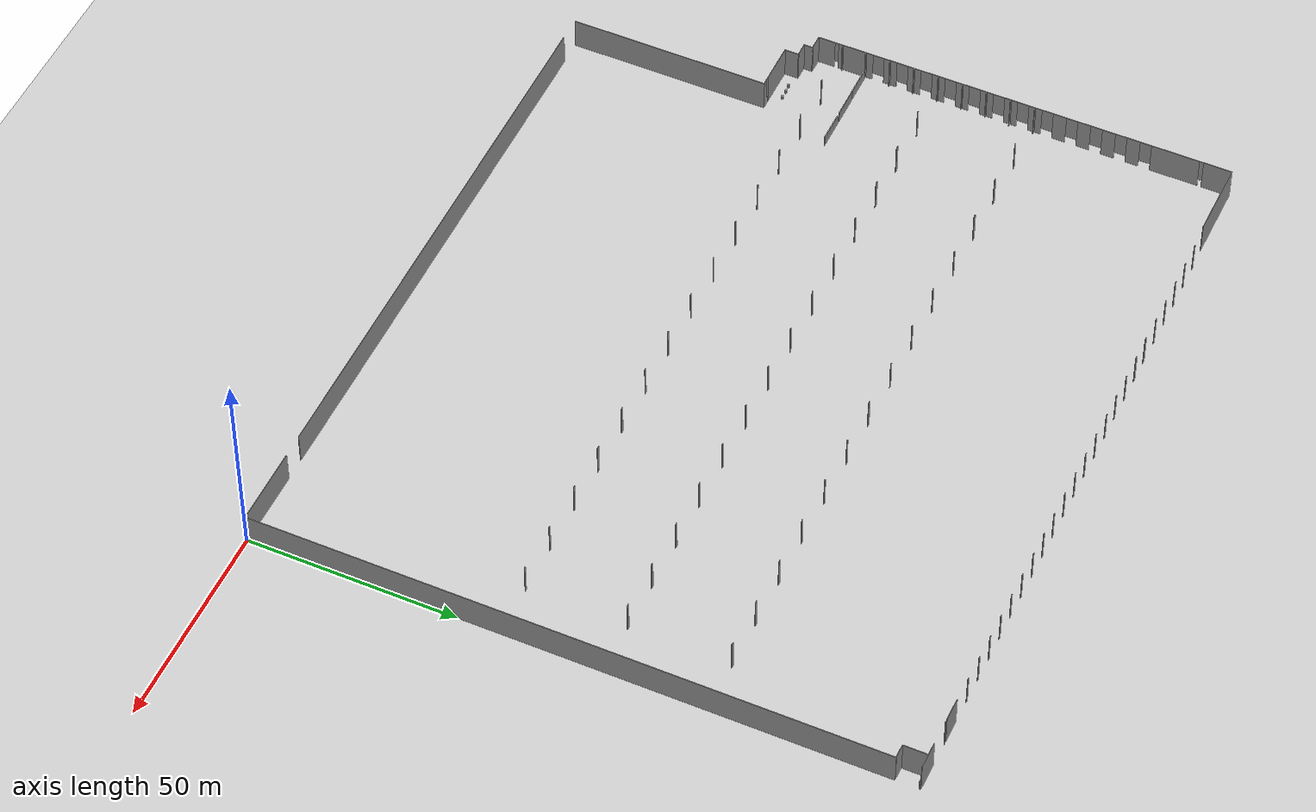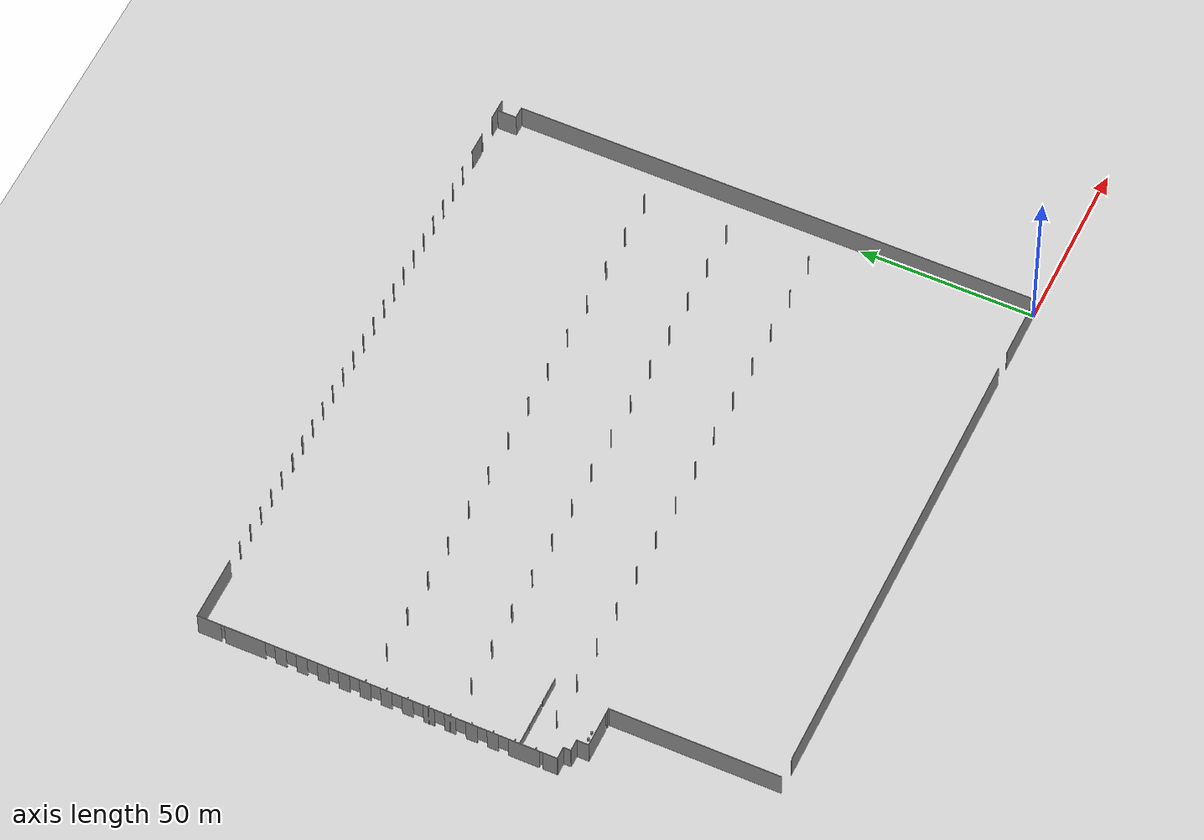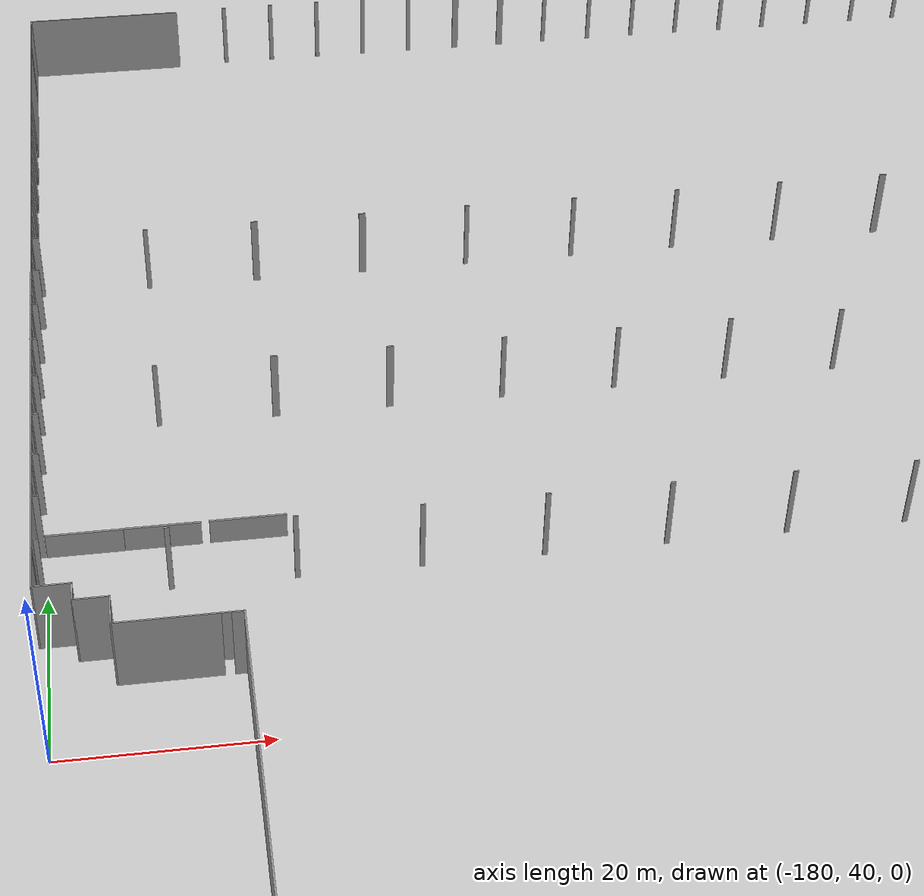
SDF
<sdf version="1.7">
 <world name="default">
  <light name="sun" type="directional">
   <pose>0 0 10 0 -0 0</pose>
   <diffuse>0.8 0.8 0.8 1</diffuse>
   <specular>0.2 0.2 0.2 1</specular>
   <attenuation>
    <range>1000</range>
    <constant>0.9</constant>
    <linear>0.01</linear>
    <quadratic>0.001</quadratic>
   </attenuation>
   <direction>-0.5 0.1 -0.9</direction>
   <spot><inner_angle>0</inner_angle><outer_angle>0</outer_angle><falloff>0</falloff></spot>
  </light>
  <model name="ground_plane">
   <static>1</static>
   <link name="link">
    <collision name="collision">
     <geometry><plane><normal>0 0 1</normal><size>100 100</size></plane></geometry>
     <surface><friction><ode><mu>100</mu><mu2>50</mu2></ode></friction></surface>
    </collision>
    <visual name="visual">
     <cast_shadows>0</cast_shadows>
     <geometry><plane><normal>0 0 1</normal><size>100 100</size></plane></geometry>
     <material>
      <script><uri>file://media/materials/scripts/gazebo.material</uri><name>Gazebo/Grey</name></script>
     </material>
    </visual>
   </link>
  </model>
  <gravity>0 0 -9.8</gravity>
  <magnetic_field>6e-06 2.3e-05 -4.2e-05</magnetic_field>
  <atmosphere type="adiabatic"/>
  <physics type="ode">
   <max_step_size>0.001</max_step_size>
   <real_time_factor>1</real_time_factor>
   <real_time_update_rate>1000</real_time_update_rate>
  </physics>
  <scene><ambient>0.4 0.4 0.4 1</ambient><background>0.7 0.7 0.7 1</background><shadows>1</shadows></scene>
  <audio><device>default</device></audio>
  <spherical_coordinates>
   <surface_model>EARTH_WGS84</surface_model>
   <latitude_deg>0</latitude_deg>
   <longitude_deg>0</longitude_deg>
   <elevation>0</elevation>
   <heading_deg>0</heading_deg>
  </spherical_coordinates>
  <model name="grey_wall">
   <static>1</static>
   <link name="link">
    <pose>0 0 1.4 0 -0 0</pose>
    <collision name="collision"><geometry><box><size>7.5 0.2 2.8</size></box></geometry></collision>
    <visual name="visual">
     <cast_shadows>0</cast_shadows>
     <geometry><box><size>7.5 0.2 2.8</size></box></geometry>
     <material>
      <script>
       <uri>model://grey_wall/materials/scripts</uri>
       <uri>model://grey_wall/materials/textures</uri>
       <name>vrc/grey_wall</name>
      </script>
     </material>
    </visual>
   </link>
   <pose>-176.336 65.7978 0 0 -0 0</pose>
  </model>
  <model name="AM_Wall">
   <pose>-90.484 78.0434 0 0 -0 0</pose>
   <link name="Wall_10">
    <collision name="Wall_10_Collision">
     <geometry><box><size>3.517 0.15 8</size></box></geometry>
     <pose>0 0 4 0 -0 0</pose>
    </collision>
    <visual name="Wall_10_Visual">
     <pose>0 0 4 0 -0 0</pose>
     <geometry><box><size>3.517 0.15 8</size></box></geometry>
     <material>
      <script><uri>file://media/materials/scripts/gazebo.material</uri><name>Gazebo/Grey</name></script>
      <ambient>1 1 1 1</ambient>
     </material>
     <meta><layer>0</layer></meta>
    </visual>
    <pose>-83.398 -28.0385 0 0 -0 1.5708</pose>
   </link>
   <link name="Wall_100">
    <collision name="Wall_100_Collision">
     <geometry><box><size>0.5 0.15 8</size></box></geometry>
     <pose>0 0 4 0 -0 0</pose>
    </collision>
    <visual name="Wall_100_Visual">
     <pose>0 0 4 0 -0 0</pose>
     <geometry><box><size>0.5 0.15 8</size></box></geometry>
     <material>
      <script><uri>file://media/materials/scripts/gazebo.material</uri><name>Gazebo/Grey</name></script>
      <ambient>1 1 1 1</ambient>
     </material>
     <meta><layer>0</layer></meta>
    </visual>
    <pose>-65.913 -18.132 0 0 -0 0</pose>
   </link>
   <link name="Wall_102">
    <collision name="Wall_102_Collision">
     <geometry><box><size>0.5 0.15 8</size></box></geometry>
     <pose>0 0 4 0 -0 0</pose>
    </collision>
    <visual name="Wall_102_Visual">
     <pose>0 0 4 0 -0 0</pose>
     <geometry><box><size>0.5 0.15 8</size></box></geometry>
     <material>
      <script><uri>file://media/materials/scripts/gazebo.material</uri><name>Gazebo/Grey</name></script>
      <ambient>1 1 1 1</ambient>
     </material>
     <meta><layer>0</layer></meta>
    </visual>
    <pose>-53.906 -18.109 0 0 -0 0</pose>
   </link>
   <link name="Wall_104">
    <collision name="Wall_104_Collision">
     <geometry><box><size>0.5 0.15 8</size></box></geometry>
     <pose>0 0 4 0 -0 0</pose>
    </collision>
    <visual name="Wall_104_Visual">
     <pose>0 0 4 0 -0 0</pose>
     <geometry><box><size>0.5 0.15 8</size></box></geometry>
     <material>
      <script><uri>file://media/materials/scripts/gazebo.material</uri><name>Gazebo/Grey</name></script>
      <ambient>1 1 1 1</ambient>
     </material>
     <meta><layer>0</layer></meta>
    </visual>
    <pose>-41.958 -18.129 0 0 -0 0</pose>
   </link>
   <link name="Wall_106">
    <collision name="Wall_106_Collision">
     <geometry><box><size>0.5 0.15 8</size></box></geometry>
     <pose>0 0 4 0 -0 0</pose>
    </collision>
    <visual name="Wall_106_Visual">
     <pose>0 0 4 0 -0 0</pose>
     <geometry><box><size>0.5 0.15 8</size></box></geometry>
     <material>
      <script><uri>file://media/materials/scripts/gazebo.material</uri><name>Gazebo/Grey</name></script>
      <ambient>1 1 1 1</ambient>
     </material>
     <meta><layer>0</layer></meta>
    </visual>
    <pose>-29.93 -18.129 0 0 -0 0</pose>
   </link>
   <link name="Wall_108">
    <collision name="Wall_108_Collision">
     <geometry><box><size>0.5 0.15 8</size></box></geometry>
     <pose>0 0 4 0 -0 0</pose>
    </collision>
    <visual name="Wall_108_Visual">
     <pose>0 0 4 0 -0 0</pose>
     <geometry><box><size>0.5 0.15 8</size></box></geometry>
     <material>
      <script><uri>file://media/materials/scripts/gazebo.material</uri><name>Gazebo/Grey</name></script>
      <ambient>1 1 1 1</ambient>
     </material>
     <meta><layer>0</layer></meta>
    </visual>
    <pose>-17.943 -18.109 0 0 -0 0</pose>
   </link>
   <link name="Wall_11">
    <collision name="Wall_11_Collision">
     <geometry><box><size>3.5 0.15 8</size></box></geometry>
     <pose>0 0 4 0 -0 0</pose>
    </collision>
    <visual name="Wall_11_Visual">
     <pose>0 0 4 0 -0 0</pose>
     <geometry><box><size>3.5 0.15 8</size></box></geometry>
     <material>
      <script><uri>file://media/materials/scripts/gazebo.material</uri><name>Gazebo/Grey</name></script>
      <ambient>1 1 1 1</ambient>
     </material>
     <meta><layer>0</layer></meta>
    </visual>
    <pose>-85.073 -26.355 0 0 -0 3.14159</pose>
   </link>
   <link name="Wall_110">
    <collision name="Wall_110_Collision">
     <geometry><box><size>0.5 0.15 8</size></box></geometry>
     <pose>0 0 4 0 -0 0</pose>
    </collision>
    <visual name="Wall_110_Visual">
     <pose>0 0 4 0 -0 0</pose>
     <geometry><box><size>0.5 0.15 8</size></box></geometry>
     <material>
      <script><uri>file://media/materials/scripts/gazebo.material</uri><name>Gazebo/Grey</name></script>
      <ambient>1 1 1 1</ambient>
     </material>
     <meta><layer>0</layer></meta>
    </visual>
    <pose>-6.01501 -18.149 0 0 -0 0</pose>
   </link>
   <link name="Wall_112">
    <collision name="Wall_112_Collision">
     <geometry><box><size>0.5 0.15 8</size></box></geometry>
     <pose>0 0 4 0 -0 0</pose>
    </collision>
    <visual name="Wall_112_Visual">
     <pose>0 0 4 0 -0 0</pose>
     <geometry><box><size>0.5 0.15 8</size></box></geometry>
     <material>
      <script><uri>file://media/materials/scripts/gazebo.material</uri><name>Gazebo/Grey</name></script>
      <ambient>1 1 1 1</ambient>
     </material>
     <meta><layer>0</layer></meta>
    </visual>
    <pose>6.01299 -18.19 0 0 -0 0</pose>
   </link>
   <link name="Wall_114">
    <collision name="Wall_114_Collision">
     <geometry><box><size>0.5 0.15 8</size></box></geometry>
     <pose>0 0 4 0 -0 0</pose>
    </collision>
    <visual name="Wall_114_Visual">
     <pose>0 0 4 0 -0 0</pose>
     <geometry><box><size>0.5 0.15 8</size></box></geometry>
     <material>
      <script><uri>file://media/materials/scripts/gazebo.material</uri><name>Gazebo/Grey</name></script>
      <ambient>1 1 1 1</ambient>
     </material>
     <meta><layer>0</layer></meta>
    </visual>
    <pose>17.9 -18.129 0 0 -0 0</pose>
   </link>
   <link name="Wall_116">
    <collision name="Wall_116_Collision">
     <geometry><box><size>0.75 0.15 8</size></box></geometry>
     <pose>0 0 4 0 -0 0</pose>
    </collision>
    <visual name="Wall_116_Visual">
     <pose>0 0 4 0 -0 0</pose>
     <geometry><box><size>0.75 0.15 8</size></box></geometry>
     <material>
      <script><uri>file://media/materials/scripts/gazebo.material</uri><name>Gazebo/Grey</name></script>
      <ambient>1 1 1 1</ambient>
     </material>
     <meta><layer>0</layer></meta>
    </visual>
    <pose>30.033 -18.089 0 0 -0 0</pose>
   </link>
   <link name="Wall_118">
    <collision name="Wall_118_Collision">
     <geometry><box><size>0.75 0.15 8</size></box></geometry>
     <pose>0 0 4 0 -0 0</pose>
    </collision>
    <visual name="Wall_118_Visual">
     <pose>0 0 4 0 -0 0</pose>
     <geometry><box><size>0.75 0.15 8</size></box></geometry>
     <material>
      <script><uri>file://media/materials/scripts/gazebo.material</uri><name>Gazebo/Grey</name></script>
      <ambient>1 1 1 1</ambient>
     </material>
     <meta><layer>0</layer></meta>
    </visual>
    <pose>42.015 -18.095 0 0 -0 0</pose>
   </link>
   <link name="Wall_12">
    <collision name="Wall_12_Collision">
     <geometry><box><size>2.25 0.15 8</size></box></geometry>
     <pose>0 0 4 0 -0 0</pose>
    </collision>
    <visual name="Wall_12_Visual">
     <pose>0 0 4 0 -0 0</pose>
     <geometry><box><size>2.25 0.15 8</size></box></geometry>
     <material>
      <script><uri>file://media/materials/scripts/gazebo.material</uri><name>Gazebo/Grey</name></script>
      <ambient>1 1 1 1</ambient>
     </material>
     <meta><layer>0</layer></meta>
    </visual>
    <pose>-86.748 -25.305 0 0 -0 1.5708</pose>
   </link>
   <link name="Wall_120">
    <collision name="Wall_120_Collision">
     <geometry><box><size>0.5 0.15 8</size></box></geometry>
     <pose>0 0 4 0 -0 0</pose>
    </collision>
    <visual name="Wall_120_Visual">
     <pose>0 0 4 0 -0 0</pose>
     <geometry><box><size>0.5 0.15 8</size></box></geometry>
     <material>
      <script><uri>file://media/materials/scripts/gazebo.material</uri><name>Gazebo/Grey</name></script>
      <ambient>1 1 1 1</ambient>
     </material>
     <meta><layer>0</layer></meta>
    </visual>
    <pose>53.918 -18.118 0 0 -0 0</pose>
   </link>
   <link name="Wall_122">
    <collision name="Wall_122_Collision">
     <geometry><box><size>0.5 0.15 8</size></box></geometry>
     <pose>0 0 4 0 -0 0</pose>
    </collision>
    <visual name="Wall_122_Visual">
     <pose>0 0 4 0 -0 0</pose>
     <geometry><box><size>0.5 0.15 8</size></box></geometry>
     <material>
      <script><uri>file://media/materials/scripts/gazebo.material</uri><name>Gazebo/Grey</name></script>
      <ambient>1 1 1 1</ambient>
     </material>
     <meta><layer>0</layer></meta>
    </visual>
    <pose>65.946 -18.118 0 0 -0 0</pose>
   </link>
   <link name="Wall_124">
    <collision name="Wall_124_Collision">
     <geometry><box><size>0.5 0.15 8</size></box></geometry>
     <pose>0 0 4 0 -0 0</pose>
    </collision>
    <visual name="Wall_124_Visual">
     <pose>0 0 4 0 -0 0</pose>
     <geometry><box><size>0.5 0.15 8</size></box></geometry>
     <material>
      <script><uri>file://media/materials/scripts/gazebo.material</uri><name>Gazebo/Grey</name></script>
      <ambient>1 1 1 1</ambient>
     </material>
     <meta><layer>0</layer></meta>
    </visual>
    <pose>77.927 -18.095 0 0 -0 0</pose>
   </link>
   <link name="Wall_126">
    <collision name="Wall_126_Collision">
     <geometry><box><size>0.5 0.15 8</size></box></geometry>
     <pose>0 0 4 0 -0 0</pose>
    </collision>
    <visual name="Wall_126_Visual">
     <pose>0 0 4 0 -0 0</pose>
     <geometry><box><size>0.5 0.15 8</size></box></geometry>
     <material>
      <script><uri>file://media/materials/scripts/gazebo.material</uri><name>Gazebo/Grey</name></script>
      <ambient>1 1 1 1</ambient>
     </material>
     <meta><layer>0</layer></meta>
    </visual>
    <pose>-77.954 5.86801 0 0 -0 0</pose>
   </link>
   <link name="Wall_128">
    <collision name="Wall_128_Collision">
     <geometry><box><size>0.75 0.15 8</size></box></geometry>
     <pose>0 0 4 0 -0 0</pose>
    </collision>
    <visual name="Wall_128_Visual">
     <pose>0 0 4 0 -0 0</pose>
     <geometry><box><size>0.75 0.15 8</size></box></geometry>
     <material>
      <script><uri>file://media/materials/scripts/gazebo.material</uri><name>Gazebo/Grey</name></script>
      <ambient>1 1 1 1</ambient>
     </material>
     <meta><layer>0</layer></meta>
    </visual>
    <pose>-65.814 5.88501 0 0 -0 0</pose>
   </link>
   <link name="Wall_130">
    <collision name="Wall_130_Collision">
     <geometry><box><size>0.75 0.15 8</size></box></geometry>
     <pose>0 0 4 0 -0 0</pose>
    </collision>
    <visual name="Wall_130_Visual">
     <pose>0 0 4 0 -0 0</pose>
     <geometry><box><size>0.75 0.15 8</size></box></geometry>
     <material>
      <script><uri>file://media/materials/scripts/gazebo.material</uri><name>Gazebo/Grey</name></script>
      <ambient>1 1 1 1</ambient>
     </material>
     <meta><layer>0</layer></meta>
    </visual>
    <pose>-53.868 5.92001 0 0 -0 0</pose>
   </link>
   <link name="Wall_132">
    <collision name="Wall_132_Collision">
     <geometry><box><size>0.5 0.15 8</size></box></geometry>
     <pose>0 0 4 0 -0 0</pose>
    </collision>
    <visual name="Wall_132_Visual">
     <pose>0 0 4 0 -0 0</pose>
     <geometry><box><size>0.5 0.15 8</size></box></geometry>
     <material>
      <script><uri>file://media/materials/scripts/gazebo.material</uri><name>Gazebo/Grey</name></script>
      <ambient>1 1 1 1</ambient>
     </material>
     <meta><layer>0</layer></meta>
    </visual>
    <pose>-41.977 5.86801 0 0 -0 0</pose>
   </link>
   <link name="Wall_134">
    <collision name="Wall_134_Collision">
     <geometry><box><size>0.5 0.15 8</size></box></geometry>
     <pose>0 0 4 0 -0 0</pose>
    </collision>
    <visual name="Wall_134_Visual">
     <pose>0 0 4 0 -0 0</pose>
     <geometry><box><size>0.5 0.15 8</size></box></geometry>
     <material>
      <script><uri>file://media/materials/scripts/gazebo.material</uri><name>Gazebo/Grey</name></script>
      <ambient>1 1 1 1</ambient>
     </material>
     <meta><layer>0</layer></meta>
    </visual>
    <pose>-29.944 5.90301 0 0 -0 0</pose>
   </link>
   <link name="Wall_136">
    <collision name="Wall_136_Collision">
     <geometry><box><size>0.5 0.15 8</size></box></geometry>
     <pose>0 0 4 0 -0 0</pose>
    </collision>
    <visual name="Wall_136_Visual">
     <pose>0 0 4 0 -0 0</pose>
     <geometry><box><size>0.5 0.15 8</size></box></geometry>
     <material>
      <script><uri>file://media/materials/scripts/gazebo.material</uri><name>Gazebo/Grey</name></script>
      <ambient>1 1 1 1</ambient>
     </material>
     <meta><layer>0</layer></meta>
    </visual>
    <pose>-18.016 5.90301 0 0 -0 0</pose>
   </link>
   <link name="Wall_138">
    <collision name="Wall_138_Collision">
     <geometry><box><size>0.5 0.15 8</size></box></geometry>
     <pose>0 0 4 0 -0 0</pose>
    </collision>
    <visual name="Wall_138_Visual">
     <pose>0 0 4 0 -0 0</pose>
     <geometry><box><size>0.5 0.15 8</size></box></geometry>
     <material>
      <script><uri>file://media/materials/scripts/gazebo.material</uri><name>Gazebo/Grey</name></script>
      <ambient>1 1 1 1</ambient>
     </material>
     <meta><layer>0</layer></meta>
    </visual>
    <pose>-6.08801 5.92001 0 0 -0 0</pose>
   </link>
   <link name="Wall_140">
    <collision name="Wall_140_Collision">
     <geometry><box><size>0.5 0.15 8</size></box></geometry>
     <pose>0 0 4 0 -0 0</pose>
    </collision>
    <visual name="Wall_140_Visual">
     <pose>0 0 4 0 -0 0</pose>
     <geometry><box><size>0.5 0.15 8</size></box></geometry>
     <material>
      <script><uri>file://media/materials/scripts/gazebo.material</uri><name>Gazebo/Grey</name></script>
      <ambient>1 1 1 1</ambient>
     </material>
     <meta><layer>0</layer></meta>
    </visual>
    <pose>5.92799 5.90301 0 0 -0 0</pose>
   </link>
   <link name="Wall_142">
    <collision name="Wall_142_Collision">
     <geometry><box><size>0.5 0.15 8</size></box></geometry>
     <pose>0 0 4 0 -0 0</pose>
    </collision>
    <visual name="Wall_142_Visual">
     <pose>0 0 4 0 -0 0</pose>
     <geometry><box><size>0.5 0.15 8</size></box></geometry>
     <material>
      <script><uri>file://media/materials/scripts/gazebo.material</uri><name>Gazebo/Grey</name></script>
      <ambient>1 1 1 1</ambient>
     </material>
     <meta><layer>0</layer></meta>
    </visual>
    <pose>17.944 5.92001 0 0 -0 0</pose>
   </link>
   <link name="Wall_144">
    <collision name="Wall_144_Collision">
     <geometry><box><size>0.5 0.15 8</size></box></geometry>
     <pose>0 0 4 0 -0 0</pose>
    </collision>
    <visual name="Wall_144_Visual">
     <pose>0 0 4 0 -0 0</pose>
     <geometry><box><size>0.5 0.15 8</size></box></geometry>
     <material>
      <script><uri>file://media/materials/scripts/gazebo.material</uri><name>Gazebo/Grey</name></script>
      <ambient>1 1 1 1</ambient>
     </material>
     <meta><layer>0</layer></meta>
    </visual>
    <pose>29.942 5.86801 0 0 -0 0</pose>
   </link>
   <link name="Wall_146">
    <collision name="Wall_146_Collision">
     <geometry><box><size>0.75 0.15 8</size></box></geometry>
     <pose>0 0 4 0 -0 0</pose>
    </collision>
    <visual name="Wall_146_Visual">
     <pose>0 0 4 0 -0 0</pose>
     <geometry><box><size>0.75 0.15 8</size></box></geometry>
     <material>
      <script><uri>file://media/materials/scripts/gazebo.material</uri><name>Gazebo/Grey</name></script>
      <ambient>1 1 1 1</ambient>
     </material>
     <meta><layer>0</layer></meta>
    </visual>
    <pose>41.995 5.86801 0 0 -0 0</pose>
   </link>
   <link name="Wall_148">
    <collision name="Wall_148_Collision">
     <geometry><box><size>0.75 0.15 8</size></box></geometry>
     <pose>0 0 4 0 -0 0</pose>
    </collision>
    <visual name="Wall_148_Visual">
     <pose>0 0 4 0 -0 0</pose>
     <geometry><box><size>0.75 0.15 8</size></box></geometry>
     <material>
      <script><uri>file://media/materials/scripts/gazebo.material</uri><name>Gazebo/Grey</name></script>
      <ambient>1 1 1 1</ambient>
     </material>
     <meta><layer>0</layer></meta>
    </visual>
    <pose>54.028 5.95501 0 0 -0 0</pose>
   </link>
   <link name="Wall_150">
    <collision name="Wall_150_Collision">
     <geometry><box><size>0.75 0.15 8</size></box></geometry>
     <pose>0 0 4 0 -0 0</pose>
    </collision>
    <visual name="Wall_150_Visual">
     <pose>0 0 4 0 -0 0</pose>
     <geometry><box><size>0.75 0.15 8</size></box></geometry>
     <material>
      <script><uri>file://media/materials/scripts/gazebo.material</uri><name>Gazebo/Grey</name></script>
      <ambient>1 1 1 1</ambient>
     </material>
     <meta><layer>0</layer></meta>
    </visual>
    <pose>65.974 5.86801 0 0 -0 0</pose>
   </link>
   <link name="Wall_152">
    <collision name="Wall_152_Collision">
     <geometry><box><size>0.75 0.15 8</size></box></geometry>
     <pose>0 0 4 0 -0 0</pose>
    </collision>
    <visual name="Wall_152_Visual">
     <pose>0 0 4 0 -0 0</pose>
     <geometry><box><size>0.75 0.15 8</size></box></geometry>
     <material>
      <script><uri>file://media/materials/scripts/gazebo.material</uri><name>Gazebo/Grey</name></script>
      <ambient>1 1 1 1</ambient>
     </material>
     <meta><layer>0</layer></meta>
    </visual>
    <pose>77.99 5.86801 0 0 -0 0</pose>
   </link>
   <link name="Wall_154">
    <collision name="Wall_154_Collision">
     <geometry><box><size>0.75 0.15 8</size></box></geometry>
     <pose>0 0 4 0 -0 0</pose>
    </collision>
    <visual name="Wall_154_Visual">
     <pose>0 0 4 0 -0 0</pose>
     <geometry><box><size>0.75 0.15 8</size></box></geometry>
     <material>
      <script><uri>file://media/materials/scripts/gazebo.material</uri><name>Gazebo/Grey</name></script>
      <ambient>1 1 1 1</ambient>
     </material>
     <meta><layer>0</layer></meta>
    </visual>
    <pose>77.979 29.894 0 0 -0 0</pose>
   </link>
   <link name="Wall_156">
    <collision name="Wall_156_Collision">
     <geometry><box><size>0.75 0.15 8</size></box></geometry>
     <pose>0 0 4 0 -0 0</pose>
    </collision>
    <visual name="Wall_156_Visual">
     <pose>0 0 4 0 -0 0</pose>
     <geometry><box><size>0.75 0.15 8</size></box></geometry>
     <material>
      <script><uri>file://media/materials/scripts/gazebo.material</uri><name>Gazebo/Grey</name></script>
      <ambient>1 1 1 1</ambient>
     </material>
     <meta><layer>0</layer></meta>
    </visual>
    <pose>65.991 29.894 0 0 -0 0</pose>
   </link>
   <link name="Wall_158">
    <collision name="Wall_158_Collision">
     <geometry><box><size>0.75 0.15 8</size></box></geometry>
     <pose>0 0 4 0 -0 0</pose>
    </collision>
    <visual name="Wall_158_Visual">
     <pose>0 0 4 0 -0 0</pose>
     <geometry><box><size>0.75 0.15 8</size></box></geometry>
     <material>
      <script><uri>file://media/materials/scripts/gazebo.material</uri><name>Gazebo/Grey</name></script>
      <ambient>1 1 1 1</ambient>
     </material>
     <meta><layer>0</layer></meta>
    </visual>
    <pose>54.004 29.914 0 0 -0 0</pose>
   </link>
   <link name="Wall_16">
    <collision name="Wall_16_Collision">
     <geometry><box><size>3.75 0.15 8</size></box></geometry>
     <pose>0 0 4 0 -0 0</pose>
    </collision>
    <visual name="Wall_16_Visual">
     <pose>0 0 4 0 -0 0</pose>
     <geometry><box><size>3.75 0.15 8</size></box></geometry>
     <material>
      <script><uri>file://media/materials/scripts/gazebo.material</uri><name>Gazebo/Grey</name></script>
      <ambient>1 1 1 1</ambient>
     </material>
     <meta><layer>0</layer></meta>
    </visual>
    <pose>-88.548 -24.255 0 0 -0 3.14159</pose>
   </link>
   <link name="Wall_160">
    <collision name="Wall_160_Collision">
     <geometry><box><size>0.5 0.15 8</size></box></geometry>
     <pose>0 0 4 0 -0 0</pose>
    </collision>
    <visual name="Wall_160_Visual">
     <pose>0 0 4 0 -0 0</pose>
     <geometry><box><size>0.5 0.15 8</size></box></geometry>
     <material>
      <script><uri>file://media/materials/scripts/gazebo.material</uri><name>Gazebo/Grey</name></script>
      <ambient>1 1 1 1</ambient>
     </material>
     <meta><layer>0</layer></meta>
    </visual>
    <pose>41.931 29.834 0 0 -0 0</pose>
   </link>
   <link name="Wall_162">
    <collision name="Wall_162_Collision">
     <geometry><box><size>0.5 0.15 8</size></box></geometry>
     <pose>0 0 4 0 -0 0</pose>
    </collision>
    <visual name="Wall_162_Visual">
     <pose>0 0 4 0 -0 0</pose>
     <geometry><box><size>0.5 0.15 8</size></box></geometry>
     <material>
      <script><uri>file://media/materials/scripts/gazebo.material</uri><name>Gazebo/Grey</name></script>
      <ambient>1 1 1 1</ambient>
     </material>
     <meta><layer>0</layer></meta>
    </visual>
    <pose>29.923 29.854 0 0 -0 0</pose>
   </link>
   <link name="Wall_164">
    <collision name="Wall_164_Collision">
     <geometry><box><size>0.5 0.15 8</size></box></geometry>
     <pose>0 0 4 0 -0 0</pose>
    </collision>
    <visual name="Wall_164_Visual">
     <pose>0 0 4 0 -0 0</pose>
     <geometry><box><size>0.5 0.15 8</size></box></geometry>
     <material>
      <script><uri>file://media/materials/scripts/gazebo.material</uri><name>Gazebo/Grey</name></script>
      <ambient>1 1 1 1</ambient>
     </material>
     <meta><layer>0</layer></meta>
    </visual>
    <pose>17.936 29.854 0 0 -0 0</pose>
   </link>
   <link name="Wall_166">
    <collision name="Wall_166_Collision">
     <geometry><box><size>0.75 0.15 8</size></box></geometry>
     <pose>0 0 4 0 -0 0</pose>
    </collision>
    <visual name="Wall_166_Visual">
     <pose>0 0 4 0 -0 0</pose>
     <geometry><box><size>0.75 0.15 8</size></box></geometry>
     <material>
      <script><uri>file://media/materials/scripts/gazebo.material</uri><name>Gazebo/Grey</name></script>
      <ambient>1 1 1 1</ambient>
     </material>
     <meta><layer>0</layer></meta>
    </visual>
    <pose>6.05299 29.874 0 0 -0 0</pose>
   </link>
   <link name="Wall_168">
    <collision name="Wall_168_Collision">
     <geometry><box><size>0.5 0.15 8</size></box></geometry>
     <pose>0 0 4 0 -0 0</pose>
    </collision>
    <visual name="Wall_168_Visual">
     <pose>0 0 4 0 -0 0</pose>
     <geometry><box><size>0.5 0.15 8</size></box></geometry>
     <material>
      <script><uri>file://media/materials/scripts/gazebo.material</uri><name>Gazebo/Grey</name></script>
      <ambient>1 1 1 1</ambient>
     </material>
     <meta><layer>0</layer></meta>
    </visual>
    <pose>-6.01901 29.894 0 0 -0 0</pose>
   </link>
   <link name="Wall_17">
    <pose>-90.348 26.67 0 0 -0 1.5708</pose>
    <visual name="Wall_17_Visual_0">
     <pose>-48.8954 0 4 0 -0 0</pose>
     <geometry><box><size>4.20921 0.15 8</size></box></geometry>
     <material>
      <script><uri>file://media/materials/scripts/gazebo.material</uri><name>Gazebo/Grey</name></script>
      <ambient>1 1 1 1</ambient>
     </material>
     <meta><layer>0</layer></meta>
    </visual>
    <collision name="Wall_17_Collision_0">
     <geometry><box><size>4.20921 0.15 8</size></box></geometry>
     <pose>-48.8954 0 4 0 -0 0</pose>
    </collision>
    <visual name="Wall_17_Visual_1">
     <pose>-41.5368 0 4 0 -0 0</pose>
     <geometry><box><size>8.70797 0.15 8</size></box></geometry>
     <material>
      <script><uri>file://media/materials/scripts/gazebo.material</uri><name>Gazebo/Grey</name></script>
      <ambient>1 1 1 1</ambient>
     </material>
     <meta><layer>0</layer></meta>
    </visual>
    <collision name="Wall_17_Collision_1">
     <geometry><box><size>8.70797 0.15 8</size></box></geometry>
     <pose>-41.5368 0 4 0 -0 0</pose>
    </collision>
    <visual name="Wall_17_Visual_2">
     <pose>-32.823 0 4 0 -0 0</pose>
     <geometry><box><size>3.2326 0.15 8</size></box></geometry>
     <material>
      <script><uri>file://media/materials/scripts/gazebo.material</uri><name>Gazebo/Grey</name></script>
      <ambient>1 1 1 1</ambient>
     </material>
     <meta><layer>0</layer></meta>
    </visual>
    <collision name="Wall_17_Collision_2">
     <geometry><box><size>3.2326 0.15 8</size></box></geometry>
     <pose>-32.823 0 4 0 -0 0</pose>
    </collision>
    <visual name="Wall_17_Visual_3">
     <pose>-26.8406 0 4 0 -0 0</pose>
     <geometry><box><size>3.24213 0.15 8</size></box></geometry>
     <material>
      <script><uri>file://media/materials/scripts/gazebo.material</uri><name>Gazebo/Grey</name></script>
      <ambient>1 1 1 1</ambient>
     </material>
     <meta><layer>0</layer></meta>
    </visual>
    <collision name="Wall_17_Collision_3">
     <geometry><box><size>3.24213 0.15 8</size></box></geometry>
     <pose>-26.8406 0 4 0 -0 0</pose>
    </collision>
    <visual name="Wall_17_Visual_4">
     <pose>-20.8082 0 4 0 -0 0</pose>
     <geometry><box><size>3.2182 0.15 8</size></box></geometry>
     <material>
      <script><uri>file://media/materials/scripts/gazebo.material</uri><name>Gazebo/Grey</name></script>
      <ambient>1 1 1 1</ambient>
     </material>
     <meta><layer>0</layer></meta>
    </visual>
    <collision name="Wall_17_Collision_4">
     <geometry><box><size>3.2182 0.15 8</size></box></geometry>
     <pose>-20.8082 0 4 0 -0 0</pose>
    </collision>
    <visual name="Wall_17_Visual_5">
     <pose>-14.7991 0 4 0 -0 0</pose>
     <geometry><box><size>3.21936 0.15 8</size></box></geometry>
     <material>
      <script><uri>file://media/materials/scripts/gazebo.material</uri><name>Gazebo/Grey</name></script>
      <ambient>1 1 1 1</ambient>
     </material>
     <meta><layer>0</layer></meta>
    </visual>
    <collision name="Wall_17_Collision_5">
     <geometry><box><size>3.21936 0.15 8</size></box></geometry>
     <pose>-14.7991 0 4 0 -0 0</pose>
    </collision>
    <visual name="Wall_17_Visual_6">
     <pose>-8.81504 0 4 0 -0 0</pose>
     <geometry><box><size>3.1983 0.15 8</size></box></geometry>
     <material>
      <script><uri>file://media/materials/scripts/gazebo.material</uri><name>Gazebo/Grey</name></script>
      <ambient>1 1 1 1</ambient>
     </material>
     <meta><layer>0</layer></meta>
    </visual>
    <collision name="Wall_17_Collision_6">
     <geometry><box><size>3.1983 0.15 8</size></box></geometry>
     <pose>-8.81504 0 4 0 -0 0</pose>
    </collision>
    <visual name="Wall_17_Visual_7">
     <pose>-2.81126 0 4 0 -0 0</pose>
     <geometry><box><size>3.1983 0.15 8</size></box></geometry>
     <material>
      <script><uri>file://media/materials/scripts/gazebo.material</uri><name>Gazebo/Grey</name></script>
      <ambient>1 1 1 1</ambient>
     </material>
     <meta><layer>0</layer></meta>
    </visual>
    <collision name="Wall_17_Collision_7">
     <geometry><box><size>3.1983 0.15 8</size></box></geometry>
     <pose>-2.81126 0 4 0 -0 0</pose>
    </collision>
    <visual name="Wall_17_Visual_8">
     <pose>3.19252 0 4 0 -0 0</pose>
     <geometry><box><size>3.22854 0.15 8</size></box></geometry>
     <material>
      <script><uri>file://media/materials/scripts/gazebo.material</uri><name>Gazebo/Grey</name></script>
      <ambient>1 1 1 1</ambient>
     </material>
     <meta><layer>0</layer></meta>
    </visual>
    <collision name="Wall_17_Collision_8">
     <geometry><box><size>3.22854 0.15 8</size></box></geometry>
     <pose>3.19252 0 4 0 -0 0</pose>
    </collision>
    <visual name="Wall_17_Visual_9">
     <pose>9.17362 0 4 0 -0 0</pose>
     <geometry><box><size>3.24367 0.15 8</size></box></geometry>
     <material>
      <script><uri>file://media/materials/scripts/gazebo.material</uri><name>Gazebo/Grey</name></script>
      <ambient>1 1 1 1</ambient>
     </material>
     <meta><layer>0</layer></meta>
    </visual>
    <collision name="Wall_17_Collision_9">
     <geometry><box><size>3.24367 0.15 8</size></box></geometry>
     <pose>9.17362 0 4 0 -0 0</pose>
    </collision>
    <visual name="Wall_17_Visual_10">
     <pose>15.1472 0 4 0 -0 0</pose>
     <geometry><box><size>3.18317 0.15 8</size></box></geometry>
     <material>
      <script><uri>file://media/materials/scripts/gazebo.material</uri><name>Gazebo/Grey</name></script>
      <ambient>1 1 1 1</ambient>
     </material>
     <meta><layer>0</layer></meta>
    </visual>
    <collision name="Wall_17_Collision_10">
     <geometry><box><size>3.18317 0.15 8</size></box></geometry>
     <pose>15.1472 0 4 0 -0 0</pose>
    </collision>
    <visual name="Wall_17_Visual_11">
     <pose>21.1812 0 4 0 -0 0</pose>
     <geometry><box><size>3.18318 0.15 8</size></box></geometry>
     <material>
      <script><uri>file://media/materials/scripts/gazebo.material</uri><name>Gazebo/Grey</name></script>
      <ambient>1 1 1 1</ambient>
     </material>
     <meta><layer>0</layer></meta>
    </visual>
    <collision name="Wall_17_Collision_11">
     <geometry><box><size>3.18318 0.15 8</size></box></geometry>
     <pose>21.1812 0 4 0 -0 0</pose>
    </collision>
    <visual name="Wall_17_Visual_12">
     <pose>27.1812 0 4 0 -0 0</pose>
     <geometry><box><size>3.2361 0.15 8</size></box></geometry>
     <material>
      <script><uri>file://media/materials/scripts/gazebo.material</uri><name>Gazebo/Grey</name></script>
      <ambient>1 1 1 1</ambient>
     </material>
     <meta><layer>0</layer></meta>
    </visual>
    <collision name="Wall_17_Collision_12">
     <geometry><box><size>3.2361 0.15 8</size></box></geometry>
     <pose>27.1812 0 4 0 -0 0</pose>
    </collision>
    <visual name="Wall_17_Visual_13">
     <pose>37.366 0 4 0 -0 0</pose>
     <geometry><box><size>11.6134 0.15 8</size></box></geometry>
     <material>
      <script><uri>file://media/materials/scripts/gazebo.material</uri><name>Gazebo/Grey</name></script>
      <ambient>1 1 1 1</ambient>
     </material>
     <meta><layer>0</layer></meta>
    </visual>
    <collision name="Wall_17_Collision_13">
     <geometry><box><size>11.6134 0.15 8</size></box></geometry>
     <pose>37.366 0 4 0 -0 0</pose>
    </collision>
    <visual name="Wall_17_Visual_14">
     <pose>47.5666 0 4 0 -0 0</pose>
     <geometry><box><size>6.86677 0.15 8</size></box></geometry>
     <material>
      <script><uri>file://media/materials/scripts/gazebo.material</uri><name>Gazebo/Grey</name></script>
      <ambient>1 1 1 1</ambient>
     </material>
     <meta><layer>0</layer></meta>
    </visual>
    <collision name="Wall_17_Collision_14">
     <geometry><box><size>6.86677 0.15 8</size></box></geometry>
     <pose>47.5666 0 4 0 -0 0</pose>
    </collision>
    <visual name="Wall_17_Visual_15">
     <pose>-46.3408 0 5 0 -0 0</pose>
     <geometry><box><size>0.9 0.15 6</size></box></geometry>
     <material>
      <script><uri>file://media/materials/scripts/gazebo.material</uri><name>Gazebo/Grey</name></script>
      <ambient>1 1 1 1</ambient>
     </material>
     <meta><layer>0</layer></meta>
    </visual>
    <collision name="Wall_17_Collision_15">
     <geometry><box><size>0.9 0.15 6</size></box></geometry>
     <pose>-46.3408 0 5 0 -0 0</pose>
    </collision>
    <visual name="Wall_17_Visual_16">
     <pose>-35.8111 0 5 0 -0 0</pose>
     <geometry><box><size>2.74352 0.15 6</size></box></geometry>
     <material>
      <script><uri>file://media/materials/scripts/gazebo.material</uri><name>Gazebo/Grey</name></script>
      <ambient>1 1 1 1</ambient>
     </material>
     <meta><layer>0</layer></meta>
    </visual>
    <collision name="Wall_17_Collision_16">
     <geometry><box><size>2.74352 0.15 6</size></box></geometry>
     <pose>-35.8111 0 5 0 -0 0</pose>
    </collision>
    <visual name="Wall_17_Visual_17">
     <pose>-29.8342 0 5 0 -0 0</pose>
     <geometry><box><size>2.74499 0.15 6</size></box></geometry>
     <material>
      <script><uri>file://media/materials/scripts/gazebo.material</uri><name>Gazebo/Grey</name></script>
      <ambient>1 1 1 1</ambient>
     </material>
     <meta><layer>0</layer></meta>
    </visual>
    <collision name="Wall_17_Collision_17">
     <geometry><box><size>2.74499 0.15 6</size></box></geometry>
     <pose>-29.8342 0 5 0 -0 0</pose>
    </collision>
    <visual name="Wall_17_Visual_18">
     <pose>-23.8185 0 5 0 -0 0</pose>
     <geometry><box><size>2.80224 0.15 6</size></box></geometry>
     <material>
      <script><uri>file://media/materials/scripts/gazebo.material</uri><name>Gazebo/Grey</name></script>
      <ambient>1 1 1 1</ambient>
     </material>
     <meta><layer>0</layer></meta>
    </visual>
    <collision name="Wall_17_Collision_18">
     <geometry><box><size>2.80224 0.15 6</size></box></geometry>
     <pose>-23.8185 0 5 0 -0 0</pose>
    </collision>
    <visual name="Wall_17_Visual_19">
     <pose>-17.804 0 5 0 -0 0</pose>
     <geometry><box><size>2.79036 0.15 6</size></box></geometry>
     <material>
      <script><uri>file://media/materials/scripts/gazebo.material</uri><name>Gazebo/Grey</name></script>
      <ambient>1 1 1 1</ambient>
     </material>
     <meta><layer>0</layer></meta>
    </visual>
    <collision name="Wall_17_Collision_19">
     <geometry><box><size>2.79036 0.15 6</size></box></geometry>
     <pose>-17.804 0 5 0 -0 0</pose>
    </collision>
    <visual name="Wall_17_Visual_20">
     <pose>-11.8018 0 5 0 -0 0</pose>
     <geometry><box><size>2.77524 0.15 6</size></box></geometry>
     <material>
      <script><uri>file://media/materials/scripts/gazebo.material</uri><name>Gazebo/Grey</name></script>
      <ambient>1 1 1 1</ambient>
     </material>
     <meta><layer>0</layer></meta>
    </visual>
    <collision name="Wall_17_Collision_20">
     <geometry><box><size>2.77524 0.15 6</size></box></geometry>
     <pose>-11.8018 0 5 0 -0 0</pose>
    </collision>
    <visual name="Wall_17_Visual_21">
     <pose>-5.81315 0 5 0 -0 0</pose>
     <geometry><box><size>2.80548 0.15 6</size></box></geometry>
     <material>
      <script><uri>file://media/materials/scripts/gazebo.material</uri><name>Gazebo/Grey</name></script>
      <ambient>1 1 1 1</ambient>
     </material>
     <meta><layer>0</layer></meta>
    </visual>
    <collision name="Wall_17_Collision_21">
     <geometry><box><size>2.80548 0.15 6</size></box></geometry>
     <pose>-5.81315 0 5 0 -0 0</pose>
    </collision>
    <visual name="Wall_17_Visual_22">
     <pose>0.183069 0 5 0 -0 0</pose>
     <geometry><box><size>2.79036 0.15 6</size></box></geometry>
     <material>
      <script><uri>file://media/materials/scripts/gazebo.material</uri><name>Gazebo/Grey</name></script>
      <ambient>1 1 1 1</ambient>
     </material>
     <meta><layer>0</layer></meta>
    </visual>
    <collision name="Wall_17_Collision_22">
     <geometry><box><size>2.79036 0.15 6</size></box></geometry>
     <pose>0.183069 0 5 0 -0 0</pose>
    </collision>
    <visual name="Wall_17_Visual_23">
     <pose>6.17929 0 5 0 -0 0</pose>
     <geometry><box><size>2.74499 0.15 6</size></box></geometry>
     <material>
      <script><uri>file://media/materials/scripts/gazebo.material</uri><name>Gazebo/Grey</name></script>
      <ambient>1 1 1 1</ambient>
     </material>
     <meta><layer>0</layer></meta>
    </visual>
    <collision name="Wall_17_Collision_23">
     <geometry><box><size>2.74499 0.15 6</size></box></geometry>
     <pose>6.17929 0 5 0 -0 0</pose>
    </collision>
    <visual name="Wall_17_Visual_24">
     <pose>12.1755 0 5 0 -0 0</pose>
     <geometry><box><size>2.76011 0.15 6</size></box></geometry>
     <material>
      <script><uri>file://media/materials/scripts/gazebo.material</uri><name>Gazebo/Grey</name></script>
      <ambient>1 1 1 1</ambient>
     </material>
     <meta><layer>0</layer></meta>
    </visual>
    <collision name="Wall_17_Collision_24">
     <geometry><box><size>2.76011 0.15 6</size></box></geometry>
     <pose>12.1755 0 5 0 -0 0</pose>
    </collision>
    <visual name="Wall_17_Visual_25">
     <pose>18.1642 0 5 0 -0 0</pose>
     <geometry><box><size>2.85085 0.15 6</size></box></geometry>
     <material>
      <script><uri>file://media/materials/scripts/gazebo.material</uri><name>Gazebo/Grey</name></script>
      <ambient>1 1 1 1</ambient>
     </material>
     <meta><layer>0</layer></meta>
    </visual>
    <collision name="Wall_17_Collision_25">
     <geometry><box><size>2.85085 0.15 6</size></box></geometry>
     <pose>18.1642 0 5 0 -0 0</pose>
    </collision>
    <visual name="Wall_17_Visual_26">
     <pose>24.1679 0 5 0 -0 0</pose>
     <geometry><box><size>2.79036 0.15 6</size></box></geometry>
     <material>
      <script><uri>file://media/materials/scripts/gazebo.material</uri><name>Gazebo/Grey</name></script>
      <ambient>1 1 1 1</ambient>
     </material>
     <meta><layer>0</layer></meta>
    </visual>
    <collision name="Wall_17_Collision_26">
     <geometry><box><size>2.79036 0.15 6</size></box></geometry>
     <pose>24.1679 0 5 0 -0 0</pose>
    </collision>
    <visual name="Wall_17_Visual_27">
     <pose>30.1793 0 5 0 -0 0</pose>
     <geometry><box><size>2.76011 0.15 6</size></box></geometry>
     <material>
      <script><uri>file://media/materials/scripts/gazebo.material</uri><name>Gazebo/Grey</name></script>
      <ambient>1 1 1 1</ambient>
     </material>
     <meta><layer>0</layer></meta>
    </visual>
    <collision name="Wall_17_Collision_27">
     <geometry><box><size>2.76011 0.15 6</size></box></geometry>
     <pose>30.1793 0 5 0 -0 0</pose>
    </collision>
    <visual name="Wall_17_Visual_28">
     <pose>43.653 0 5 0 -0 0</pose>
     <geometry><box><size>0.960491 0.15 6</size></box></geometry>
     <material>
      <script><uri>file://media/materials/scripts/gazebo.material</uri><name>Gazebo/Grey</name></script>
      <ambient>1 1 1 1</ambient>
     </material>
     <meta><layer>0</layer></meta>
    </visual>
    <collision name="Wall_17_Collision_28">
     <geometry><box><size>0.960491 0.15 6</size></box></geometry>
     <pose>43.653 0 5 0 -0 0</pose>
    </collision>
   </link>
   <link name="Wall_170">
    <collision name="Wall_170_Collision">
     <geometry><box><size>0.5 0.15 8</size></box></geometry>
     <pose>0 0 4 0 -0 0</pose>
    </collision>
    <visual name="Wall_170_Visual">
     <pose>0 0 4 0 -0 0</pose>
     <geometry><box><size>0.5 0.15 8</size></box></geometry>
     <material>
      <script><uri>file://media/materials/scripts/gazebo.material</uri><name>Gazebo/Grey</name></script>
      <ambient>1 1 1 1</ambient>
     </material>
     <meta><layer>0</layer></meta>
    </visual>
    <pose>-17.967 29.874 0 0 -0 0</pose>
   </link>
   <link name="Wall_172">
    <collision name="Wall_172_Collision">
     <geometry><box><size>0.5 0.15 8</size></box></geometry>
     <pose>0 0 4 0 -0 0</pose>
    </collision>
    <visual name="Wall_172_Visual">
     <pose>0 0 4 0 -0 0</pose>
     <geometry><box><size>0.5 0.15 8</size></box></geometry>
     <material>
      <script><uri>file://media/materials/scripts/gazebo.material</uri><name>Gazebo/Grey</name></script>
      <ambient>1 1 1 1</ambient>
     </material>
     <meta><layer>0</layer></meta>
    </visual>
    <pose>-29.805 29.853 0 0 -0 3.14159</pose>
   </link>
   <link name="Wall_174">
    <collision name="Wall_174_Collision">
     <geometry><box><size>0.5 0.15 8</size></box></geometry>
     <pose>0 0 4 0 -0 0</pose>
    </collision>
    <visual name="Wall_174_Visual">
     <pose>0 0 4 0 -0 0</pose>
     <geometry><box><size>0.5 0.15 8</size></box></geometry>
     <material>
      <script><uri>file://media/materials/scripts/gazebo.material</uri><name>Gazebo/Grey</name></script>
      <ambient>1 1 1 1</ambient>
     </material>
     <meta><layer>0</layer></meta>
    </visual>
    <pose>-41.986 29.873 0 0 -0 0</pose>
   </link>
   <link name="Wall_176">
    <collision name="Wall_176_Collision">
     <geometry><box><size>0.75 0.15 8</size></box></geometry>
     <pose>0 0 4 0 -0 0</pose>
    </collision>
    <visual name="Wall_176_Visual">
     <pose>0 0 4 0 -0 0</pose>
     <geometry><box><size>0.75 0.15 8</size></box></geometry>
     <material>
      <script><uri>file://media/materials/scripts/gazebo.material</uri><name>Gazebo/Grey</name></script>
      <ambient>1 1 1 1</ambient>
     </material>
     <meta><layer>0</layer></meta>
    </visual>
    <pose>-53.828 29.873 0 0 -0 0</pose>
   </link>
   <link name="Wall_178">
    <collision name="Wall_178_Collision">
     <geometry><box><size>0.75 0.15 8</size></box></geometry>
     <pose>0 0 4 0 -0 0</pose>
    </collision>
    <visual name="Wall_178_Visual">
     <pose>0 0 4 0 -0 0</pose>
     <geometry><box><size>0.75 0.15 8</size></box></geometry>
     <material>
      <script><uri>file://media/materials/scripts/gazebo.material</uri><name>Gazebo/Grey</name></script>
      <ambient>1 1 1 1</ambient>
     </material>
     <meta><layer>0</layer></meta>
    </visual>
    <pose>-65.876 29.853 0 0 -0 0</pose>
   </link>
   <link name="Wall_180">
    <collision name="Wall_180_Collision">
     <geometry><box><size>0.5 0.15 8</size></box></geometry>
     <pose>0 0 4 0 -0 0</pose>
    </collision>
    <visual name="Wall_180_Visual">
     <pose>0 0 4 0 -0 0</pose>
     <geometry><box><size>0.5 0.15 8</size></box></geometry>
     <material>
      <script><uri>file://media/materials/scripts/gazebo.material</uri><name>Gazebo/Grey</name></script>
      <ambient>1 1 1 1</ambient>
     </material>
     <meta><layer>0</layer></meta>
    </visual>
    <pose>-77.914 29.866 0 0 -0 0</pose>
   </link>
   <link name="Wall_182">
    <collision name="Wall_182_Collision">
     <geometry><box><size>0.75 0.15 8</size></box></geometry>
     <pose>0 0 4 0 -0 0</pose>
    </collision>
    <visual name="Wall_182_Visual">
     <pose>0 0 4 0 -0 0</pose>
     <geometry><box><size>0.75 0.15 8</size></box></geometry>
     <material>
      <script><uri>file://media/materials/scripts/gazebo.material</uri><name>Gazebo/Grey</name></script>
      <ambient>1 1 1 1</ambient>
     </material>
     <meta><layer>0</layer></meta>
    </visual>
    <pose>-89.894 29.846 0 0 -0 3.14159</pose>
   </link>
   <link name="Wall_184">
    <collision name="Wall_184_Collision">
     <geometry><box><size>0.75 0.15 8</size></box></geometry>
     <pose>0 0 4 0 -0 0</pose>
    </collision>
    <visual name="Wall_184_Visual">
     <pose>0 0 4 0 -0 0</pose>
     <geometry><box><size>0.75 0.15 8</size></box></geometry>
     <material>
      <script><uri>file://media/materials/scripts/gazebo.material</uri><name>Gazebo/Grey</name></script>
      <ambient>1 1 1 1</ambient>
     </material>
     <meta><layer>0</layer></meta>
    </visual>
    <pose>-89.874 23.912 0 0 -0 3.14159</pose>
   </link>
   <link name="Wall_186">
    <collision name="Wall_186_Collision">
     <geometry><box><size>0.75 0.15 8</size></box></geometry>
     <pose>0 0 4 0 -0 0</pose>
    </collision>
    <visual name="Wall_186_Visual">
     <pose>0 0 4 0 -0 0</pose>
     <geometry><box><size>0.75 0.15 8</size></box></geometry>
     <material>
      <script><uri>file://media/materials/scripts/gazebo.material</uri><name>Gazebo/Grey</name></script>
      <ambient>1 1 1 1</ambient>
     </material>
     <meta><layer>0</layer></meta>
    </visual>
    <pose>-90.038 17.878 0 0 -0 0</pose>
   </link>
   <link name="Wall_188">
    <collision name="Wall_188_Collision">
     <geometry><box><size>0.75 0.15 8</size></box></geometry>
     <pose>0 0 4 0 -0 0</pose>
    </collision>
    <visual name="Wall_188_Visual">
     <pose>0 0 4 0 -0 0</pose>
     <geometry><box><size>0.75 0.15 8</size></box></geometry>
     <material>
      <script><uri>file://media/materials/scripts/gazebo.material</uri><name>Gazebo/Grey</name></script>
      <ambient>1 1 1 1</ambient>
     </material>
     <meta><layer>0</layer></meta>
    </visual>
    <pose>-90.118 11.924 0 0 -0 0</pose>
   </link>
   <link name="Wall_190">
    <collision name="Wall_190_Collision">
     <geometry><box><size>0.75 0.15 8</size></box></geometry>
     <pose>0 0 4 0 -0 0</pose>
    </collision>
    <visual name="Wall_190_Visual">
     <pose>0 0 4 0 -0 0</pose>
     <geometry><box><size>0.75 0.15 8</size></box></geometry>
     <material>
      <script><uri>file://media/materials/scripts/gazebo.material</uri><name>Gazebo/Grey</name></script>
      <ambient>1 1 1 1</ambient>
     </material>
     <meta><layer>0</layer></meta>
    </visual>
    <pose>-90.058 5.91001 0 0 -0 0</pose>
   </link>
   <link name="Wall_192">
    <collision name="Wall_192_Collision">
     <geometry><box><size>0.75 0.15 8</size></box></geometry>
     <pose>0 0 4 0 -0 0</pose>
    </collision>
    <visual name="Wall_192_Visual">
     <pose>0 0 4 0 -0 0</pose>
     <geometry><box><size>0.75 0.15 8</size></box></geometry>
     <material>
      <script><uri>file://media/materials/scripts/gazebo.material</uri><name>Gazebo/Grey</name></script>
      <ambient>1 1 1 1</ambient>
     </material>
     <meta><layer>0</layer></meta>
    </visual>
    <pose>-90.018 -0.143993 0 0 -0 0</pose>
   </link>
   <link name="Wall_194">
    <collision name="Wall_194_Collision">
     <geometry><box><size>0.75 0.15 8</size></box></geometry>
     <pose>0 0 4 0 -0 0</pose>
    </collision>
    <visual name="Wall_194_Visual">
     <pose>0 0 4 0 -0 0</pose>
     <geometry><box><size>0.75 0.15 8</size></box></geometry>
     <material>
      <script><uri>file://media/materials/scripts/gazebo.material</uri><name>Gazebo/Grey</name></script>
      <ambient>1 1 1 1</ambient>
     </material>
     <meta><layer>0</layer></meta>
    </visual>
    <pose>-89.998 -6.13799 0 0 -0 0</pose>
   </link>
   <link name="Wall_196">
    <collision name="Wall_196_Collision">
     <geometry><box><size>0.75 0.15 8</size></box></geometry>
     <pose>0 0 4 0 -0 0</pose>
    </collision>
    <visual name="Wall_196_Visual">
     <pose>0 0 4 0 -0 0</pose>
     <geometry><box><size>0.75 0.15 8</size></box></geometry>
     <material>
      <script><uri>file://media/materials/scripts/gazebo.material</uri><name>Gazebo/Grey</name></script>
      <ambient>1 1 1 1</ambient>
     </material>
     <meta><layer>0</layer></meta>
    </visual>
    <pose>-90.038 -12.212 0 0 -0 0</pose>
   </link>
   <link name="Wall_21">
    <collision name="Wall_21_Collision">
     <geometry><box><size>18.5 0.15 8</size></box></geometry>
     <pose>0 0 4 0 -0 0</pose>
    </collision>
    <visual name="Wall_21_Visual">
     <pose>0 0 4 0 -0 0</pose>
     <geometry><box><size>18.5 0.15 8</size></box></geometry>
     <material>
      <script><uri>file://media/materials/scripts/gazebo.material</uri><name>Gazebo/Grey</name></script>
      <ambient>1 1 1 1</ambient>
     </material>
     <meta><layer>0</layer></meta>
    </visual>
    <pose>-81.173 77.595 0 0 -0 0</pose>
   </link>
   <link name="Wall_25">
    <collision name="Wall_25_Collision">
     <geometry><box><size>0.5 0.15 8</size></box></geometry>
     <pose>0 0 4 0 -0 0</pose>
    </collision>
    <visual name="Wall_25_Visual">
     <pose>0 0 4 0 -0 0</pose>
     <geometry><box><size>0.5 0.15 8</size></box></geometry>
     <material>
      <script><uri>file://media/materials/scripts/gazebo.material</uri><name>Gazebo/Grey</name></script>
      <ambient>1 1 1 1</ambient>
     </material>
     <meta><layer>0</layer></meta>
    </visual>
    <pose>-65.882 77.895 0 0 -0 0</pose>
   </link>
   <link name="Wall_27">
    <collision name="Wall_27_Collision">
     <geometry><box><size>0.5 0.15 8</size></box></geometry>
     <pose>0 0 4 0 -0 0</pose>
    </collision>
    <visual name="Wall_27_Visual">
     <pose>0 0 4 0 -0 0</pose>
     <geometry><box><size>0.5 0.15 8</size></box></geometry>
     <material>
      <script><uri>file://media/materials/scripts/gazebo.material</uri><name>Gazebo/Grey</name></script>
      <ambient>1 1 1 1</ambient>
     </material>
     <meta><layer>0</layer></meta>
    </visual>
    <pose>-59.938 77.895 0 0 -0 0</pose>
   </link>
   <link name="Wall_29">
    <collision name="Wall_29_Collision">
     <geometry><box><size>0.5 0.15 8</size></box></geometry>
     <pose>0 0 4 0 -0 0</pose>
    </collision>
    <visual name="Wall_29_Visual">
     <pose>0 0 4 0 -0 0</pose>
     <geometry><box><size>0.5 0.15 8</size></box></geometry>
     <material>
      <script><uri>file://media/materials/scripts/gazebo.material</uri><name>Gazebo/Grey</name></script>
      <ambient>1 1 1 1</ambient>
     </material>
     <meta><layer>0</layer></meta>
    </visual>
    <pose>-53.947 77.907 0 0 -0 0</pose>
   </link>
   <link name="Wall_31">
    <collision name="Wall_31_Collision">
     <geometry><box><size>0.5 0.15 8</size></box></geometry>
     <pose>0 0 4 0 -0 0</pose>
    </collision>
    <visual name="Wall_31_Visual">
     <pose>0 0 4 0 -0 0</pose>
     <geometry><box><size>0.5 0.15 8</size></box></geometry>
     <material>
      <script><uri>file://media/materials/scripts/gazebo.material</uri><name>Gazebo/Grey</name></script>
      <ambient>1 1 1 1</ambient>
     </material>
     <meta><layer>0</layer></meta>
    </visual>
    <pose>-47.951 77.907 0 0 -0 0</pose>
   </link>
   <link name="Wall_33">
    <collision name="Wall_33_Collision">
     <geometry><box><size>0.5 0.15 8</size></box></geometry>
     <pose>0 0 4 0 -0 0</pose>
    </collision>
    <visual name="Wall_33_Visual">
     <pose>0 0 4 0 -0 0</pose>
     <geometry><box><size>0.5 0.15 8</size></box></geometry>
     <material>
      <script><uri>file://media/materials/scripts/gazebo.material</uri><name>Gazebo/Grey</name></script>
      <ambient>1 1 1 1</ambient>
     </material>
     <meta><layer>0</layer></meta>
    </visual>
    <pose>-41.975 77.887 0 0 -0 0</pose>
   </link>
   <link name="Wall_35">
    <collision name="Wall_35_Collision">
     <geometry><box><size>0.75 0.15 8</size></box></geometry>
     <pose>0 0 4 0 -0 0</pose>
    </collision>
    <visual name="Wall_35_Visual">
     <pose>0 0 4 0 -0 0</pose>
     <geometry><box><size>0.75 0.15 8</size></box></geometry>
     <material>
      <script><uri>file://media/materials/scripts/gazebo.material</uri><name>Gazebo/Grey</name></script>
      <ambient>1 1 1 1</ambient>
     </material>
     <meta><layer>0</layer></meta>
    </visual>
    <pose>-35.775 77.837 0 0 -0 0</pose>
   </link>
   <link name="Wall_37">
    <collision name="Wall_37_Collision">
     <geometry><box><size>0.75 0.15 8</size></box></geometry>
     <pose>0 0 4 0 -0 0</pose>
    </collision>
    <visual name="Wall_37_Visual">
     <pose>0 0 4 0 -0 0</pose>
     <geometry><box><size>0.75 0.15 8</size></box></geometry>
     <material>
      <script><uri>file://media/materials/scripts/gazebo.material</uri><name>Gazebo/Grey</name></script>
      <ambient>1 1 1 1</ambient>
     </material>
     <meta><layer>0</layer></meta>
    </visual>
    <pose>-29.839 77.927 0 0 -0 0</pose>
   </link>
   <link name="Wall_39">
    <collision name="Wall_39_Collision">
     <geometry><box><size>0.5 0.15 8</size></box></geometry>
     <pose>0 0 4 0 -0 0</pose>
    </collision>
    <visual name="Wall_39_Visual">
     <pose>0 0 4 0 -0 0</pose>
     <geometry><box><size>0.5 0.15 8</size></box></geometry>
     <material>
      <script><uri>file://media/materials/scripts/gazebo.material</uri><name>Gazebo/Grey</name></script>
      <ambient>1 1 1 1</ambient>
     </material>
     <meta><layer>0</layer></meta>
    </visual>
    <pose>-23.948 77.907 0 0 -0 0</pose>
   </link>
   <link name="Wall_41">
    <collision name="Wall_41_Collision">
     <geometry><box><size>0.5 0.15 8</size></box></geometry>
     <pose>0 0 4 0 -0 0</pose>
    </collision>
    <visual name="Wall_41_Visual">
     <pose>0 0 4 0 -0 0</pose>
     <geometry><box><size>0.5 0.15 8</size></box></geometry>
     <material>
      <script><uri>file://media/materials/scripts/gazebo.material</uri><name>Gazebo/Grey</name></script>
      <ambient>1 1 1 1</ambient>
     </material>
     <meta><layer>0</layer></meta>
    </visual>
    <pose>-17.942 77.907 0 0 -0 0</pose>
   </link>
   <link name="Wall_43">
    <collision name="Wall_43_Collision">
     <geometry><box><size>0.5 0.15 8</size></box></geometry>
     <pose>0 0 4 0 -0 0</pose>
    </collision>
    <visual name="Wall_43_Visual">
     <pose>0 0 4 0 -0 0</pose>
     <geometry><box><size>0.5 0.15 8</size></box></geometry>
     <material>
      <script><uri>file://media/materials/scripts/gazebo.material</uri><name>Gazebo/Grey</name></script>
      <ambient>1 1 1 1</ambient>
     </material>
     <meta><layer>0</layer></meta>
    </visual>
    <pose>-12.035 77.957 0 0 -0 0</pose>
   </link>
   <link name="Wall_45">
    <collision name="Wall_45_Collision">
     <geometry><box><size>0.5 0.15 8</size></box></geometry>
     <pose>0 0 4 0 -0 0</pose>
    </collision>
    <visual name="Wall_45_Visual">
     <pose>0 0 4 0 -0 0</pose>
     <geometry><box><size>0.5 0.15 8</size></box></geometry>
     <material>
      <script><uri>file://media/materials/scripts/gazebo.material</uri><name>Gazebo/Grey</name></script>
      <ambient>1 1 1 1</ambient>
     </material>
     <meta><layer>0</layer></meta>
    </visual>
    <pose>-6.03901 77.917 0 0 -0 0</pose>
   </link>
   <link name="Wall_47">
    <collision name="Wall_47_Collision">
     <geometry><box><size>0.5 0.15 8</size></box></geometry>
     <pose>0 0 4 0 -0 0</pose>
    </collision>
    <visual name="Wall_47_Visual">
     <pose>0 0 4 0 -0 0</pose>
     <geometry><box><size>0.5 0.15 8</size></box></geometry>
     <material>
      <script><uri>file://media/materials/scripts/gazebo.material</uri><name>Gazebo/Grey</name></script>
      <ambient>1 1 1 1</ambient>
     </material>
     <meta><layer>0</layer></meta>
    </visual>
    <pose>-0.044006 77.877 0 0 -0 0</pose>
   </link>
   <link name="Wall_49">
    <collision name="Wall_49_Collision">
     <geometry><box><size>0.5 0.15 8</size></box></geometry>
     <pose>0 0 4 0 -0 0</pose>
    </collision>
    <visual name="Wall_49_Visual">
     <pose>0 0 4 0 -0 0</pose>
     <geometry><box><size>0.5 0.15 8</size></box></geometry>
     <material>
      <script><uri>file://media/materials/scripts/gazebo.material</uri><name>Gazebo/Grey</name></script>
      <ambient>1 1 1 1</ambient>
     </material>
     <meta><layer>0</layer></meta>
    </visual>
    <pose>5.87299 77.857 0 0 -0 0</pose>
   </link>
   <link name="Wall_51">
    <collision name="Wall_51_Collision">
     <geometry><box><size>0.5 0.15 8</size></box></geometry>
     <pose>0 0 4 0 -0 0</pose>
    </collision>
    <visual name="Wall_51_Visual">
     <pose>0 0 4 0 -0 0</pose>
     <geometry><box><size>0.5 0.15 8</size></box></geometry>
     <material>
      <script><uri>file://media/materials/scripts/gazebo.material</uri><name>Gazebo/Grey</name></script>
      <ambient>1 1 1 1</ambient>
     </material>
     <meta><layer>0</layer></meta>
    </visual>
    <pose>11.938 77.847 0 0 -0 0</pose>
   </link>
   <link name="Wall_53">
    <collision name="Wall_53_Collision">
     <geometry><box><size>0.5 0.15 8</size></box></geometry>
     <pose>0 0 4 0 -0 0</pose>
    </collision>
    <visual name="Wall_53_Visual">
     <pose>0 0 4 0 -0 0</pose>
     <geometry><box><size>0.5 0.15 8</size></box></geometry>
     <material>
      <script><uri>file://media/materials/scripts/gazebo.material</uri><name>Gazebo/Grey</name></script>
      <ambient>1 1 1 1</ambient>
     </material>
     <meta><layer>0</layer></meta>
    </visual>
    <pose>18.054 77.827 0 0 -0 0</pose>
   </link>
   <link name="Wall_55">
    <collision name="Wall_55_Collision">
     <geometry><box><size>0.5 0.15 8</size></box></geometry>
     <pose>0 0 4 0 -0 0</pose>
    </collision>
    <visual name="Wall_55_Visual">
     <pose>0 0 4 0 -0 0</pose>
     <geometry><box><size>0.5 0.15 8</size></box></geometry>
     <material>
      <script><uri>file://media/materials/scripts/gazebo.material</uri><name>Gazebo/Grey</name></script>
      <ambient>1 1 1 1</ambient>
     </material>
     <meta><layer>0</layer></meta>
    </visual>
    <pose>23.95 77.857 0 0 -0 0</pose>
   </link>
   <link name="Wall_57">
    <collision name="Wall_57_Collision">
     <geometry><box><size>0.5 0.15 8</size></box></geometry>
     <pose>0 0 4 0 -0 0</pose>
    </collision>
    <visual name="Wall_57_Visual">
     <pose>0 0 4 0 -0 0</pose>
     <geometry><box><size>0.5 0.15 8</size></box></geometry>
     <material>
      <script><uri>file://media/materials/scripts/gazebo.material</uri><name>Gazebo/Grey</name></script>
      <ambient>1 1 1 1</ambient>
     </material>
     <meta><layer>0</layer></meta>
    </visual>
    <pose>29.906 77.847 0 0 -0 0</pose>
   </link>
   <link name="Wall_59">
    <collision name="Wall_59_Collision">
     <geometry><box><size>0.5 0.15 2.5</size></box></geometry>
     <pose>0 0 1.25 0 -0 0</pose>
    </collision>
    <visual name="Wall_59_Visual">
     <pose>0 0 1.25 0 -0 0</pose>
     <geometry><box><size>0.5 0.15 2.5</size></box></geometry>
     <material>
      <script><uri>file://media/materials/scripts/gazebo.material</uri><name>Gazebo/Grey</name></script>
      <ambient>1 1 1 1</ambient>
     </material>
     <meta><layer>0</layer></meta>
    </visual>
    <pose>36.002 77.847 0 0 -0 0</pose>
   </link>
   <link name="Wall_6">
    <collision name="Wall_6_Collision">
     <geometry><box><size>48.2329 0.15 8</size></box></geometry>
     <pose>0 0 4 0 -0 0</pose>
    </collision>
    <visual name="Wall_6_Visual">
     <pose>0 0 4 0 -0 0</pose>
     <geometry><box><size>48.2329 0.15 8</size></box></geometry>
     <material>
      <script><uri>file://media/materials/scripts/gazebo.material</uri><name>Gazebo/Grey</name></script>
      <ambient>1 1 1 1</ambient>
     </material>
     <meta><layer>0</layer></meta>
    </visual>
    <pose>-71.548 -53.7635 0 0 -0 -1.5708</pose>
   </link>
   <link name="Wall_60">
    <collision name="Wall_60_Collision">
     <geometry><box><size>0.5 0.15 8</size></box></geometry>
     <pose>0 0 4 0 -0 0</pose>
    </collision>
    <visual name="Wall_60_Visual">
     <pose>0 0 4 0 -0 0</pose>
     <geometry><box><size>0.5 0.15 8</size></box></geometry>
     <material>
      <script><uri>file://media/materials/scripts/gazebo.material</uri><name>Gazebo/Grey</name></script>
      <ambient>1 1 1 1</ambient>
     </material>
     <meta><layer>0</layer></meta>
    </visual>
    <pose>36.002 77.847 0 0 -0 3.14159</pose>
   </link>
   <link name="Wall_62">
    <collision name="Wall_62_Collision">
     <geometry><box><size>0.5 0.15 8</size></box></geometry>
     <pose>0 0 4 0 -0 0</pose>
    </collision>
    <visual name="Wall_62_Visual">
     <pose>0 0 4 0 -0 0</pose>
     <geometry><box><size>0.5 0.15 8</size></box></geometry>
     <material>
      <script><uri>file://media/materials/scripts/gazebo.material</uri><name>Gazebo/Grey</name></script>
      <ambient>1 1 1 1</ambient>
     </material>
     <meta><layer>0</layer></meta>
    </visual>
    <pose>41.978 77.817 0 0 -0 0</pose>
   </link>
   <link name="Wall_64">
    <collision name="Wall_64_Collision">
     <geometry><box><size>0.5 0.15 8</size></box></geometry>
     <pose>0 0 4 0 -0 0</pose>
    </collision>
    <visual name="Wall_64_Visual">
     <pose>0 0 4 0 -0 0</pose>
     <geometry><box><size>0.5 0.15 8</size></box></geometry>
     <material>
      <script><uri>file://media/materials/scripts/gazebo.material</uri><name>Gazebo/Grey</name></script>
      <ambient>1 1 1 1</ambient>
     </material>
     <meta><layer>0</layer></meta>
    </visual>
    <pose>47.974 77.867 0 0 -0 0</pose>
   </link>
   <link name="Wall_66">
    <collision name="Wall_66_Collision">
     <geometry><box><size>0.5 0.15 8</size></box></geometry>
     <pose>0 0 4 0 -0 0</pose>
    </collision>
    <visual name="Wall_66_Visual">
     <pose>0 0 4 0 -0 0</pose>
     <geometry><box><size>0.5 0.15 8</size></box></geometry>
     <material>
      <script><uri>file://media/materials/scripts/gazebo.material</uri><name>Gazebo/Grey</name></script>
      <ambient>1 1 1 1</ambient>
     </material>
     <meta><layer>0</layer></meta>
    </visual>
    <pose>53.93 77.857 0 0 -0 0</pose>
   </link>
   <link name="Wall_68">
    <collision name="Wall_68_Collision">
     <geometry><box><size>0.5 0.15 8</size></box></geometry>
     <pose>0 0 4 0 -0 0</pose>
    </collision>
    <visual name="Wall_68_Visual">
     <pose>0 0 4 0 -0 0</pose>
     <geometry><box><size>0.5 0.15 8</size></box></geometry>
     <material>
      <script><uri>file://media/materials/scripts/gazebo.material</uri><name>Gazebo/Grey</name></script>
      <ambient>1 1 1 1</ambient>
     </material>
     <meta><layer>0</layer></meta>
    </visual>
    <pose>59.896 77.877 0 0 -0 0</pose>
   </link>
   <link name="Wall_70">
    <collision name="Wall_70_Collision">
     <geometry><box><size>0.5 0.15 8</size></box></geometry>
     <pose>0 0 4 0 -0 0</pose>
    </collision>
    <visual name="Wall_70_Visual">
     <pose>0 0 4 0 -0 0</pose>
     <geometry><box><size>0.5 0.15 8</size></box></geometry>
     <material>
      <script><uri>file://media/materials/scripts/gazebo.material</uri><name>Gazebo/Grey</name></script>
      <ambient>1 1 1 1</ambient>
     </material>
     <meta><layer>0</layer></meta>
    </visual>
    <pose>65.952 77.877 0 0 -0 0</pose>
   </link>
   <link name="Wall_72">
    <collision name="Wall_72_Collision">
     <geometry><box><size>5.5 0.15 8</size></box></geometry>
     <pose>0 0 4 0 -0 0</pose>
    </collision>
    <visual name="Wall_72_Visual">
     <pose>0 0 4 0 -0 0</pose>
     <geometry><box><size>5.5 0.15 8</size></box></geometry>
     <material>
      <script><uri>file://media/materials/scripts/gazebo.material</uri><name>Gazebo/Grey</name></script>
      <ambient>1 1 1 1</ambient>
     </material>
     <meta><layer>0</layer></meta>
    </visual>
    <pose>74.537 77.827 0 0 -0 0</pose>
   </link>
   <link name="Wall_74">
    <collision name="Wall_74_Collision">
     <geometry><box><size>0.5 0.15 8</size></box></geometry>
     <pose>0 0 4 0 -0 0</pose>
    </collision>
    <visual name="Wall_74_Visual">
     <pose>0 0 4 0 -0 0</pose>
     <geometry><box><size>0.5 0.15 8</size></box></geometry>
     <material>
      <script><uri>file://media/materials/scripts/gazebo.material</uri><name>Gazebo/Grey</name></script>
      <ambient>1 1 1 1</ambient>
     </material>
     <meta><layer>0</layer></meta>
    </visual>
    <pose>77.916 77.882 0 0 -0 0</pose>
   </link>
   <link name="Wall_76">
    <collision name="Wall_76_Collision">
     <geometry><box><size>6.5 0.15 8</size></box></geometry>
     <pose>0 0 4 0 -0 0</pose>
    </collision>
    <visual name="Wall_76_Visual">
     <pose>0 0 4 0 -0 0</pose>
     <geometry><box><size>6.5 0.15 8</size></box></geometry>
     <material>
      <script><uri>file://media/materials/scripts/gazebo.material</uri><name>Gazebo/Grey</name></script>
      <ambient>1 1 1 1</ambient>
     </material>
     <meta><layer>0</layer></meta>
    </visual>
    <pose>87.202 77.843 0 0 -0 0</pose>
   </link>
   <link name="Wall_78">
    <collision name="Wall_78_Collision">
     <geometry><box><size>0.5 0.15 2.5</size></box></geometry>
     <pose>0 0 1.25 0 -0 0</pose>
    </collision>
    <visual name="Wall_78_Visual">
     <pose>0 0 1.25 0 -0 0</pose>
     <geometry><box><size>0.5 0.15 2.5</size></box></geometry>
     <material>
      <script><uri>file://media/materials/scripts/gazebo.material</uri><name>Gazebo/Grey</name></script>
      <ambient>1 1 1 1</ambient>
     </material>
     <meta><layer>0</layer></meta>
    </visual>
    <pose>90.377 77.6678 0 0 -0 -1.57063</pose>
   </link>
   <link name="Wall_79">
    <collision name="Wall_79_Collision">
     <geometry><box><size>3.5 0.15 2.5</size></box></geometry>
     <pose>0 0 1.25 0 -0 0</pose>
    </collision>
    <visual name="Wall_79_Visual">
     <pose>0 0 1.25 0 -0 0</pose>
     <geometry><box><size>3.5 0.15 2.5</size></box></geometry>
     <material>
      <script><uri>file://media/materials/scripts/gazebo.material</uri><name>Gazebo/Grey</name></script>
      <ambient>1 1 1 1</ambient>
     </material>
     <meta><layer>0</layer></meta>
    </visual>
    <pose>88.702 77.4928 0 0 -0 3.14148</pose>
   </link>
   <link name="Wall_80">
    <collision name="Wall_80_Collision">
     <geometry><box><size>5.54062 0.15 8</size></box></geometry>
     <pose>0 0 4 0 -0 0</pose>
    </collision>
    <visual name="Wall_80_Visual">
     <pose>0 0 4 0 -0 0</pose>
     <geometry><box><size>5.54062 0.15 8</size></box></geometry>
     <material>
      <script><uri>file://media/materials/scripts/gazebo.material</uri><name>Gazebo/Grey</name></script>
      <ambient>1 1 1 1</ambient>
     </material>
     <meta><layer>0</layer></meta>
    </visual>
    <pose>87.027 74.7975 0 0 -0 -1.5708</pose>
   </link>
   <link name="Wall_81">
    <collision name="Wall_81_Collision">
     <geometry><box><size>3.54094 0.15 8</size></box></geometry>
     <pose>0 0 4 0 -0 0</pose>
    </collision>
    <visual name="Wall_81_Visual">
     <pose>0 0 4 0 -0 0</pose>
     <geometry><box><size>3.54094 0.15 8</size></box></geometry>
     <material>
      <script><uri>file://media/materials/scripts/gazebo.material</uri><name>Gazebo/Grey</name></script>
      <ambient>1 1 1 1</ambient>
     </material>
     <meta><layer>0</layer></meta>
    </visual>
    <pose>88.7225 72.1025 0 0 -0 0.000295</pose>
   </link>
   <link name="Wall_84">
    <collision name="Wall_84_Collision">
     <geometry><box><size>150.21 0.15 8</size></box></geometry>
     <pose>0 0 4 0 -0 0</pose>
    </collision>
    <visual name="Wall_84_Visual">
     <pose>0 0 4 0 -0 0</pose>
     <geometry><box><size>150.21 0.15 8</size></box></geometry>
     <material>
      <script><uri>file://media/materials/scripts/gazebo.material</uri><name>Gazebo/Grey</name></script>
      <ambient>1 1 1 1</ambient>
     </material>
     <meta><layer>0</layer></meta>
    </visual>
    <pose>90.418 -2.92699 0 0 -0 -1.5708</pose>
   </link>
   <link name="Wall_86">
    <collision name="Wall_86_Collision">
     <geometry><box><size>18.75 0.15 8</size></box></geometry>
     <pose>0 0 4 0 -0 0</pose>
    </collision>
    <visual name="Wall_86_Visual">
     <pose>0 0 4 0 -0 0</pose>
     <geometry><box><size>18.75 0.15 8</size></box></geometry>
     <material>
      <script><uri>file://media/materials/scripts/gazebo.material</uri><name>Gazebo/Grey</name></script>
      <ambient>1 1 1 1</ambient>
     </material>
     <meta><layer>0</layer></meta>
    </visual>
    <pose>81.118 -77.957 0 0 -0 3.14159</pose>
   </link>
   <link name="Wall_9">
    <pose>-77.473 -29.722 0 0 -0 3.14159</pose>
    <visual name="Wall_9_Visual_0">
     <pose>-5.372 0 4 0 -0 0</pose>
     <geometry><box><size>1.256 0.15 8</size></box></geometry>
     <material>
      <script><uri>file://media/materials/scripts/gazebo.material</uri><name>Gazebo/Grey</name></script>
      <ambient>1 1 1 1</ambient>
     </material>
     <meta><layer>0</layer></meta>
    </visual>
    <collision name="Wall_9_Collision_0">
     <geometry><box><size>1.256 0.15 8</size></box></geometry>
     <pose>-5.372 0 4 0 -0 0</pose>
    </collision>
    <visual name="Wall_9_Visual_1">
     <pose>1.078 0 4 0 -0 0</pose>
     <geometry><box><size>9.844 0.15 8</size></box></geometry>
     <material>
      <script><uri>file://media/materials/scripts/gazebo.material</uri><name>Gazebo/Grey</name></script>
      <ambient>1 1 1 1</ambient>
     </material>
     <meta><layer>0</layer></meta>
    </visual>
    <collision name="Wall_9_Collision_1">
     <geometry><box><size>9.844 0.15 8</size></box></geometry>
     <pose>1.078 0 4 0 -0 0</pose>
    </collision>
    <visual name="Wall_9_Visual_2">
     <pose>-4.294 0 5 0 -0 0</pose>
     <geometry><box><size>0.9 0.15 6</size></box></geometry>
     <material>
      <script><uri>file://media/materials/scripts/gazebo.material</uri><name>Gazebo/Grey</name></script>
      <ambient>1 1 1 1</ambient>
     </material>
     <meta><layer>0</layer></meta>
    </visual>
    <collision name="Wall_9_Collision_2">
     <geometry><box><size>0.9 0.15 6</size></box></geometry>
     <pose>-4.294 0 5 0 -0 0</pose>
    </collision>
   </link>
   <link name="Wall_90">
    <collision name="Wall_90_Collision">
     <geometry><box><size>132 0.15 8</size></box></geometry>
     <pose>0 0 4 0 -0 0</pose>
    </collision>
    <visual name="Wall_90_Visual">
     <pose>0 0 4 0 -0 0</pose>
     <geometry><box><size>132 0.15 8</size></box></geometry>
     <material>
      <script><uri>file://media/materials/scripts/gazebo.material</uri><name>Gazebo/Grey</name></script>
      <ambient>1 1 1 1</ambient>
     </material>
     <meta><layer>0</layer></meta>
    </visual>
    <pose>0.291994 -77.952 0 0 -0 0</pose>
   </link>
   <link name="Wall_93">
    <collision name="Wall_93_Collision">
     <geometry><box><size>0.5 0.15 8</size></box></geometry>
     <pose>0 0 4 0 -0 0</pose>
    </collision>
    <visual name="Wall_93_Visual">
     <pose>0 0 4 0 -0 0</pose>
     <geometry><box><size>0.5 0.15 8</size></box></geometry>
     <material>
      <script><uri>file://media/materials/scripts/gazebo.material</uri><name>Gazebo/Grey</name></script>
      <ambient>1 1 1 1</ambient>
     </material>
     <meta><layer>0</layer></meta>
    </visual>
    <pose>-89.933 -18.068 0 0 -0 0</pose>
   </link>
   <link name="Wall_95">
    <collision name="Wall_95_Collision">
     <geometry><box><size>0.5 0.15 8</size></box></geometry>
     <pose>0 0 4 0 -0 0</pose>
    </collision>
    <visual name="Wall_95_Visual">
     <pose>0 0 4 0 -0 0</pose>
     <geometry><box><size>0.5 0.15 8</size></box></geometry>
     <material>
      <script><uri>file://media/materials/scripts/gazebo.material</uri><name>Gazebo/Grey</name></script>
      <ambient>1 1 1 1</ambient>
     </material>
     <meta><layer>0</layer></meta>
    </visual>
    <pose>-77.91 -18.122 0 0 -0 0</pose>
   </link>
   <static>1</static>
  </model>
  <model name="grey_wall_clone">
   <static>1</static>
   <link name="link">
    <pose>0 0 1.4 0 -0 0</pose>
    <collision name="collision"><geometry><box><size>7.5 0.2 2.8</size></box></geometry></collision>
    <visual name="visual">
     <cast_shadows>0</cast_shadows>
     <geometry><box><size>7.5 0.2 2.8</size></box></geometry>
     <material>
      <script>
       <uri>model://grey_wall/materials/scripts</uri>
       <uri>model://grey_wall/materials/textures</uri>
       <name>vrc/grey_wall</name>
      </script>
     </material>
    </visual>
   </link>
   <pose>-168.876 65.8247 0 0 -0 0</pose>
  </model>
  <model name="grey_wall_clone_0">
   <static>1</static>
   <link name="link">
    <pose>0 0 1.4 0 -0 0</pose>
    <collision name="collision"><geometry><box><size>7.5 0.2 2.8</size></box></geometry></collision>
    <visual name="visual">
     <cast_shadows>0</cast_shadows>
     <geometry><box><size>7.5 0.2 2.8</size></box></geometry>
     <material>
      <script>
       <uri>model://grey_wall/materials/scripts</uri>
       <uri>model://grey_wall/materials/textures</uri>
       <name>vrc/grey_wall</name>
      </script>
     </material>
    </visual>
   </link>
   <pose>-160.586 65.8569 0 0 -0 0</pose>
  </model>
  <model name="charger">
   <link name="link">
    <inertial>
     <mass>0.252412</mass>
     <inertia>
      <ixx>0.0262063</ixx>
      <ixy>0</ixy>
      <ixz>0</ixz>
      <iyy>0.0264845</iyy>
      <iyz>0</iyz>
      <izz>0.0106221</izz>
     </inertia>
    </inertial>
    <visual name="visual">
     <geometry><box><size>0.509025 0.495865 1</size></box></geometry>
     <material>
      <script><name>Gazebo/Grey</name><uri>file://media/materials/scripts/gazebo.material</uri></script>
      <shader type="pixel"/>
     </material>
    </visual>
    <collision name="collision">
     <geometry><box><size>0.509025 0.495865 1</size></box></geometry>
     <surface>
      <friction>
       <ode><mu>1</mu><mu2>1</mu2><fdir1>0 0 0</fdir1><slip1>0</slip1><slip2>0</slip2></ode>
       <torsional>
        <coefficient>1</coefficient>
        <patch_radius>0</patch_radius>
        <surface_radius>0</surface_radius>
        <use_patch_radius>1</use_patch_radius>
        <ode><slip>0</slip></ode>
       </torsional>
      </friction>
      <bounce><restitution_coefficient>0</restitution_coefficient><threshold>1e+06</threshold></bounce>
      <contact>
       <collide_without_contact>0</collide_without_contact>
       <collide_without_contact_bitmask>1</collide_without_contact_bitmask>
       <collide_bitmask>1</collide_bitmask>
       <ode>
        <soft_cfm>0</soft_cfm>
        <soft_erp>0.2</soft_erp>
        <kp>1e+13</kp>
        <kd>1</kd>
        <max_vel>0.01</max_vel>
        <min_depth>0</min_depth>
       </ode>
       <bullet>
        <split_impulse>1</split_impulse>
        <split_impulse_penetration_threshold>-0.01</split_impulse_penetration_threshold>
        <soft_cfm>0</soft_cfm>
        <soft_erp>0.2</soft_erp>
        <kp>1e+13</kp>
        <kd>1</kd>
       </bullet>
      </contact>
     </surface>
    </collision>
   </link>
   <static>1</static>
   <pose>-166.333 51.1189 0.5 0 -0 0</pose>
  </model>
  <model name="charger_clone">
   <link name="link">
    <inertial>
     <mass>0.252412</mass>
     <inertia>
      <ixx>0.0262063</ixx>
      <ixy>0</ixy>
      <ixz>0</ixz>
      <iyy>0.0264845</iyy>
      <iyz>0</iyz>
      <izz>0.0106221</izz>
     </inertia>
    </inertial>
    <visual name="visual">
     <geometry><box><size>0.509025 0.495865 1</size></box></geometry>
     <material>
      <script><name>Gazebo/Grey</name><uri>file://media/materials/scripts/gazebo.material</uri></script>
      <shader type="pixel"/>
     </material>
    </visual>
    <collision name="collision">
     <geometry><box><size>0.509025 0.495865 1</size></box></geometry>
     <surface>
      <friction>
       <ode><mu>1</mu><mu2>1</mu2><fdir1>0 0 0</fdir1><slip1>0</slip1><slip2>0</slip2></ode>
       <torsional>
        <coefficient>1</coefficient>
        <patch_radius>0</patch_radius>
        <surface_radius>0</surface_radius>
        <use_patch_radius>1</use_patch_radius>
        <ode><slip>0</slip></ode>
       </torsional>
      </friction>
      <bounce><restitution_coefficient>0</restitution_coefficient><threshold>1e+06</threshold></bounce>
      <contact>
       <collide_without_contact>0</collide_without_contact>
       <collide_without_contact_bitmask>1</collide_without_contact_bitmask>
       <collide_bitmask>1</collide_bitmask>
       <ode>
        <soft_cfm>0</soft_cfm>
        <soft_erp>0.2</soft_erp>
        <kp>1e+13</kp>
        <kd>1</kd>
        <max_vel>0.01</max_vel>
        <min_depth>0</min_depth>
       </ode>
       <bullet>
        <split_impulse>1</split_impulse>
        <split_impulse_penetration_threshold>-0.01</split_impulse_penetration_threshold>
        <soft_cfm>0</soft_cfm>
        <soft_erp>0.2</soft_erp>
        <kp>1e+13</kp>
        <kd>1</kd>
       </bullet>
      </contact>
     </surface>
    </collision>
   </link>
   <static>1</static>
   <pose>-168.362 51.0696 0.5 0 -0 0</pose>
  </model>
  <model name="charger_clone_clone">
   <link name="link">
    <inertial>
     <mass>0.252412</mass>
     <inertia>
      <ixx>0.0262063</ixx>
      <ixy>0</ixy>
      <ixz>0</ixz>
      <iyy>0.0264845</iyy>
      <iyz>0</iyz>
      <izz>0.0106221</izz>
     </inertia>
    </inertial>
    <visual name="visual">
     <geometry><box><size>0.509025 0.495865 1</size></box></geometry>
     <material>
      <script><name>Gazebo/Grey</name><uri>file://media/materials/scripts/gazebo.material</uri></script>
      <shader type="pixel"/>
     </material>
    </visual>
    <collision name="collision">
     <geometry><box><size>0.509025 0.495865 1</size></box></geometry>
     <surface>
      <friction>
       <ode><mu>1</mu><mu2>1</mu2><fdir1>0 0 0</fdir1><slip1>0</slip1><slip2>0</slip2></ode>
       <torsional>
        <coefficient>1</coefficient>
        <patch_radius>0</patch_radius>
        <surface_radius>0</surface_radius>
        <use_patch_radius>1</use_patch_radius>
        <ode><slip>0</slip></ode>
       </torsional>
      </friction>
      <bounce><restitution_coefficient>0</restitution_coefficient><threshold>1e+06</threshold></bounce>
      <contact>
       <collide_without_contact>0</collide_without_contact>
       <collide_without_contact_bitmask>1</collide_without_contact_bitmask>
       <collide_bitmask>1</collide_bitmask>
       <ode>
        <soft_cfm>0</soft_cfm>
        <soft_erp>0.2</soft_erp>
        <kp>1e+13</kp>
        <kd>1</kd>
        <max_vel>0.01</max_vel>
        <min_depth>0</min_depth>
       </ode>
       <bullet>
        <split_impulse>1</split_impulse>
        <split_impulse_penetration_threshold>-0.01</split_impulse_penetration_threshold>
        <soft_cfm>0</soft_cfm>
        <soft_erp>0.2</soft_erp>
        <kp>1e+13</kp>
        <kd>1</kd>
       </bullet>
      </contact>
     </surface>
    </collision>
   </link>
   <static>1</static>
   <pose>-170.18 50.9058 0.5 0 -0 0</pose>
  </model>
 </world>
</sdf>
